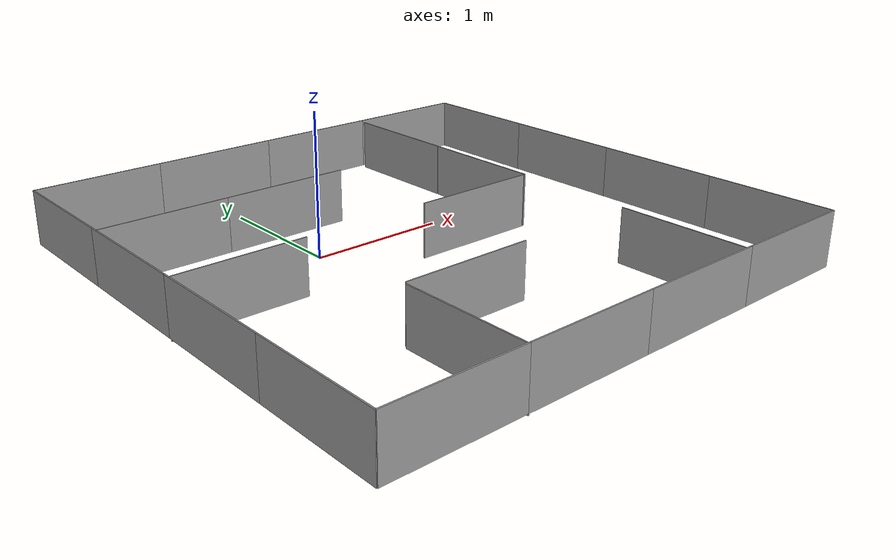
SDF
<sdf version="1.7">
 <model name="turtlebot3_maze">
  <model name="enclosure">
   <model name="wall_section_00">
    <link name="link">
     <inertial>
      <mass>0.2</mass>
      <inertia>
       <ixx>0.0333333</ixx>
       <ixy>0</ixy>
       <ixz>0</ixz>
       <iyy>0.0333333</iyy>
       <iyz>0</iyz>
       <izz>0.0333333</izz>
      </inertia>
      <pose>0 0 0 0 -0 0</pose>
     </inertial>
     <self_collide>0</self_collide>
     <enable_wind>0</enable_wind>
     <kinematic>0</kinematic>
     <pose>0 0 0 0 -0 0</pose>
     <gravity>1</gravity>
     <visual name="visual">
      <geometry>
       <box>
        <size>1 0.01 0.42</size>
       </box>
      </geometry>
      <material>
       <script>
        <name>Gazebo/Grey</name>
        <uri>file://media/materials/scripts/gazebo.material</uri>
       </script>
       <shader type="pixel">
        <normal_map>__default__</normal_map>
       </shader>
       <ambient>0.3 0.3 0.3 1</ambient>
       <diffuse>0.7 0.7 0.7 1</diffuse>
       <specular>0.01 0.01 0.01 1</specular>
       <emissive>1 1 1 1</emissive>
      </material>
      <pose>0 0 0 0 -0 0</pose>
      <transparency>0</transparency>
      <cast_shadows>1</cast_shadows>
     </visual>
     <collision name="collision_1">
      <laser_retro>0</laser_retro>
      <max_contacts>10</max_contacts>
      <pose>0 0 0 0 -0 0</pose>
      <geometry>
       <box>
        <size>1 0.01 0.42</size>
       </box>
      </geometry>
      <surface>
       <friction>
        <ode>
         <mu>1</mu>
         <mu2>1</mu2>
         <fdir1>0 0 0</fdir1>
         <slip1>0</slip1>
         <slip2>0</slip2>
        </ode>
        <torsional>
         <coefficient>1</coefficient>
         <patch_radius>0</patch_radius>
         <surface_radius>0</surface_radius>
         <use_patch_radius>1</use_patch_radius>
         <ode>
          <slip>0</slip>
         </ode>
        </torsional>
       </friction>
       <bounce>
        <restitution_coefficient>0</restitution_coefficient>
        <threshold>1e+06</threshold>
       </bounce>
       <contact>
        <collide_without_contact>0</collide_without_contact>
        <collide_without_contact_bitmask>1</collide_without_contact_bitmask>
        <collide_bitmask>1</collide_bitmask>
        <ode>
         <soft_cfm>0</soft_cfm>
         <soft_erp>0.2</soft_erp>
         <kp>1e+13</kp>
         <kd>1</kd>
         <max_vel>0.01</max_vel>
         <min_depth>0</min_depth>
        </ode>
        <bullet>
         <split_impulse>1</split_impulse>
         <split_impulse_penetration_threshold>-0.01</split_impulse_penetration_threshold>
         <soft_cfm>0</soft_cfm>
         <soft_erp>0.2</soft_erp>
         <kp>1e+13</kp>
         <kd>1</kd>
        </bullet>
       </contact>
      </surface>
     </collision>
    </link>
    <static>0</static>
    <allow_auto_disable>1</allow_auto_disable>
    <pose>-0.5 0 0 0 -0 0</pose>
   </model>
   <model name="wall_section_01">
    <link name="link">
     <inertial>
      <mass>0.2</mass>
      <inertia>
       <ixx>0.0333333</ixx>
       <ixy>0</ixy>
       <ixz>0</ixz>
       <iyy>0.0333333</iyy>
       <iyz>0</iyz>
       <izz>0.0333333</izz>
      </inertia>
      <pose>0 0 0 0 -0 0</pose>
     </inertial>
     <self_collide>0</self_collide>
     <enable_wind>0</enable_wind>
     <kinematic>0</kinematic>
     <pose>0 0 0 0 -0 0</pose>
     <gravity>1</gravity>
     <visual name="visual">
      <geometry>
       <box>
        <size>1 0.01 0.42</size>
       </box>
      </geometry>
      <material>
       <script>
        <name>Gazebo/Grey</name>
        <uri>file://media/materials/scripts/gazebo.material</uri>
       </script>
       <shader type="pixel">
        <normal_map>__default__</normal_map>
       </shader>
       <ambient>0.3 0.3 0.3 1</ambient>
       <diffuse>0.7 0.7 0.7 1</diffuse>
       <specular>0.01 0.01 0.01 1</specular>
       <emissive>1 1 1 1</emissive>
      </material>
      <pose>0 0 0 0 -0 0</pose>
      <transparency>0</transparency>
      <cast_shadows>1</cast_shadows>
     </visual>
     <collision name="collision_1">
      <laser_retro>0</laser_retro>
      <max_contacts>10</max_contacts>
      <pose>0 0 0 0 -0 0</pose>
      <geometry>
       <box>
        <size>1 0.01 0.42</size>
       </box>
      </geometry>
      <surface>
       <friction>
        <ode>
         <mu>1</mu>
         <mu2>1</mu2>
         <fdir1>0 0 0</fdir1>
         <slip1>0</slip1>
         <slip2>0</slip2>
        </ode>
        <torsional>
         <coefficient>1</coefficient>
         <patch_radius>0</patch_radius>
         <surface_radius>0</surface_radius>
         <use_patch_radius>1</use_patch_radius>
         <ode>
          <slip>0</slip>
         </ode>
        </torsional>
       </friction>
       <bounce>
        <restitution_coefficient>0</restitution_coefficient>
        <threshold>1e+06</threshold>
       </bounce>
       <contact>
        <collide_without_contact>0</collide_without_contact>
        <collide_without_contact_bitmask>1</collide_without_contact_bitmask>
        <collide_bitmask>1</collide_bitmask>
        <ode>
         <soft_cfm>0</soft_cfm>
         <soft_erp>0.2</soft_erp>
         <kp>1e+13</kp>
         <kd>1</kd>
         <max_vel>0.01</max_vel>
         <min_depth>0</min_depth>
        </ode>
        <bullet>
         <split_impulse>1</split_impulse>
         <split_impulse_penetration_threshold>-0.01</split_impulse_penetration_threshold>
         <soft_cfm>0</soft_cfm>
         <soft_erp>0.2</soft_erp>
         <kp>1e+13</kp>
         <kd>1</kd>
        </bullet>
       </contact>
      </surface>
     </collision>
    </link>
    <static>0</static>
    <allow_auto_disable>1</allow_auto_disable>
    <pose>0.5 0 0 0 -0 0</pose>
   </model>
   <model name="wall_section_02">
    <link name="link">
     <inertial>
      <mass>0.2</mass>
      <inertia>
       <ixx>0.0333333</ixx>
       <ixy>0</ixy>
       <ixz>0</ixz>
       <iyy>0.0333333</iyy>
       <iyz>0</iyz>
       <izz>0.0333333</izz>
      </inertia>
      <pose>0 0 0 0 -0 0</pose>
     </inertial>
     <self_collide>0</self_collide>
     <enable_wind>0</enable_wind>
     <kinematic>0</kinematic>
     <pose>0 0 0 0 -0 0</pose>
     <gravity>1</gravity>
     <visual name="visual">
      <geometry>
       <box>
        <size>1 0.01 0.42</size>
       </box>
      </geometry>
      <material>
       <script>
        <name>Gazebo/Grey</name>
        <uri>file://media/materials/scripts/gazebo.material</uri>
       </script>
       <shader type="pixel">
        <normal_map>__default__</normal_map>
       </shader>
       <ambient>0.3 0.3 0.3 1</ambient>
       <diffuse>0.7 0.7 0.7 1</diffuse>
       <specular>0.01 0.01 0.01 1</specular>
       <emissive>1 1 1 1</emissive>
      </material>
      <pose>0 0 0 0 -0 0</pose>
      <transparency>0</transparency>
      <cast_shadows>1</cast_shadows>
     </visual>
     <collision name="collision_1">
      <laser_retro>0</laser_retro>
      <max_contacts>10</max_contacts>
      <pose>0 0 0 0 -0 0</pose>
      <geometry>
       <box>
        <size>1 0.01 0.42</size>
       </box>
      </geometry>
      <surface>
       <friction>
        <ode>
         <mu>1</mu>
         <mu2>1</mu2>
         <fdir1>0 0 0</fdir1>
         <slip1>0</slip1>
         <slip2>0</slip2>
        </ode>
        <torsional>
         <coefficient>1</coefficient>
         <patch_radius>0</patch_radius>
         <surface_radius>0</surface_radius>
         <use_patch_radius>1</use_patch_radius>
         <ode>
          <slip>0</slip>
         </ode>
        </torsional>
       </friction>
       <bounce>
        <restitution_coefficient>0</restitution_coefficient>
        <threshold>1e+06</threshold>
       </bounce>
       <contact>
        <collide_without_contact>0</collide_without_contact>
        <collide_without_contact_bitmask>1</collide_without_contact_bitmask>
        <collide_bitmask>1</collide_bitmask>
        <ode>
         <soft_cfm>0</soft_cfm>
         <soft_erp>0.2</soft_erp>
         <kp>1e+13</kp>
         <kd>1</kd>
         <max_vel>0.01</max_vel>
         <min_depth>0</min_depth>
        </ode>
        <bullet>
         <split_impulse>1</split_impulse>
         <split_impulse_penetration_threshold>-0.01</split_impulse_penetration_threshold>
         <soft_cfm>0</soft_cfm>
         <soft_erp>0.2</soft_erp>
         <kp>1e+13</kp>
         <kd>1</kd>
        </bullet>
       </contact>
      </surface>
     </collision>
    </link>
    <static>0</static>
    <allow_auto_disable>1</allow_auto_disable>
    <pose>1.5 0 0 0 -0 0</pose>
   </model>
   <model name="wall_section_03">
    <link name="link">
     <inertial>
      <mass>0.2</mass>
      <inertia>
       <ixx>0.0333333</ixx>
       <ixy>0</ixy>
       <ixz>0</ixz>
       <iyy>0.0333333</iyy>
       <iyz>0</iyz>
       <izz>0.0333333</izz>
      </inertia>
      <pose>0 0 0 0 -0 0</pose>
     </inertial>
     <self_collide>0</self_collide>
     <enable_wind>0</enable_wind>
     <kinematic>0</kinematic>
     <pose>0 0 0 0 -0 0</pose>
     <gravity>1</gravity>
     <visual name="visual">
      <geometry>
       <box>
        <size>1 0.01 0.42</size>
       </box>
      </geometry>
      <material>
       <script>
        <name>Gazebo/Grey</name>
        <uri>file://media/materials/scripts/gazebo.material</uri>
       </script>
       <shader type="pixel">
        <normal_map>__default__</normal_map>
       </shader>
       <ambient>0.3 0.3 0.3 1</ambient>
       <diffuse>0.7 0.7 0.7 1</diffuse>
       <specular>0.01 0.01 0.01 1</specular>
       <emissive>1 1 1 1</emissive>
      </material>
      <pose>0 0 0 0 -0 0</pose>
      <transparency>0</transparency>
      <cast_shadows>1</cast_shadows>
     </visual>
     <collision name="collision_1">
      <laser_retro>0</laser_retro>
      <max_contacts>10</max_contacts>
      <pose>0 0 0 0 -0 0</pose>
      <geometry>
       <box>
        <size>1 0.01 0.42</size>
       </box>
      </geometry>
      <surface>
       <friction>
        <ode>
         <mu>1</mu>
         <mu2>1</mu2>
         <fdir1>0 0 0</fdir1>
         <slip1>0</slip1>
         <slip2>0</slip2>
        </ode>
        <torsional>
         <coefficient>1</coefficient>
         <patch_radius>0</patch_radius>
         <surface_radius>0</surface_radius>
         <use_patch_radius>1</use_patch_radius>
         <ode>
          <slip>0</slip>
         </ode>
        </torsional>
       </friction>
       <bounce>
        <restitution_coefficient>0</restitution_coefficient>
        <threshold>1e+06</threshold>
       </bounce>
       <contact>
        <collide_without_contact>0</collide_without_contact>
        <collide_without_contact_bitmask>1</collide_without_contact_bitmask>
        <collide_bitmask>1</collide_bitmask>
        <ode>
         <soft_cfm>0</soft_cfm>
         <soft_erp>0.2</soft_erp>
         <kp>1e+13</kp>
         <kd>1</kd>
         <max_vel>0.01</max_vel>
         <min_depth>0</min_depth>
        </ode>
        <bullet>
         <split_impulse>1</split_impulse>
         <split_impulse_penetration_threshold>-0.01</split_impulse_penetration_threshold>
         <soft_cfm>0</soft_cfm>
         <soft_erp>0.2</soft_erp>
         <kp>1e+13</kp>
         <kd>1</kd>
        </bullet>
       </contact>
      </surface>
     </collision>
    </link>
    <static>0</static>
    <allow_auto_disable>1</allow_auto_disable>
    <pose>2.5 0 0 0 -0 0</pose>
   </model>
   <model name="wall_section_04">
    <link name="link">
     <inertial>
      <mass>0.2</mass>
      <inertia>
       <ixx>0.0333333</ixx>
       <ixy>0</ixy>
       <ixz>0</ixz>
       <iyy>0.0333333</iyy>
       <iyz>0</iyz>
       <izz>0.0333333</izz>
      </inertia>
      <pose>0 0 0 0 -0 0</pose>
     </inertial>
     <self_collide>0</self_collide>
     <enable_wind>0</enable_wind>
     <kinematic>0</kinematic>
     <pose>0 0 0 0 -0 0</pose>
     <gravity>1</gravity>
     <visual name="visual">
      <geometry>
       <box>
        <size>1 0.01 0.42</size>
       </box>
      </geometry>
      <material>
       <script>
        <name>Gazebo/Grey</name>
        <uri>file://media/materials/scripts/gazebo.material</uri>
       </script>
       <shader type="pixel">
        <normal_map>__default__</normal_map>
       </shader>
       <ambient>0.3 0.3 0.3 1</ambient>
       <diffuse>0.7 0.7 0.7 1</diffuse>
       <specular>0.01 0.01 0.01 1</specular>
       <emissive>1 1 1 1</emissive>
      </material>
      <pose>0 0 0 0 -0 0</pose>
      <transparency>0</transparency>
      <cast_shadows>1</cast_shadows>
     </visual>
     <collision name="collision_1">
      <laser_retro>0</laser_retro>
      <max_contacts>10</max_contacts>
      <pose>0 0 0 0 -0 0</pose>
      <geometry>
       <box>
        <size>1 0.01 0.42</size>
       </box>
      </geometry>
      <surface>
       <friction>
        <ode>
         <mu>1</mu>
         <mu2>1</mu2>
         <fdir1>0 0 0</fdir1>
         <slip1>0</slip1>
         <slip2>0</slip2>
        </ode>
        <torsional>
         <coefficient>1</coefficient>
         <patch_radius>0</patch_radius>
         <surface_radius>0</surface_radius>
         <use_patch_radius>1</use_patch_radius>
         <ode>
          <slip>0</slip>
         </ode>
        </torsional>
       </friction>
       <bounce>
        <restitution_coefficient>0</restitution_coefficient>
        <threshold>1e+06</threshold>
       </bounce>
       <contact>
        <collide_without_contact>0</collide_without_contact>
        <collide_without_contact_bitmask>1</collide_without_contact_bitmask>
        <collide_bitmask>1</collide_bitmask>
        <ode>
         <soft_cfm>0</soft_cfm>
         <soft_erp>0.2</soft_erp>
         <kp>1e+13</kp>
         <kd>1</kd>
         <max_vel>0.01</max_vel>
         <min_depth>0</min_depth>
        </ode>
        <bullet>
         <split_impulse>1</split_impulse>
         <split_impulse_penetration_threshold>-0.01</split_impulse_penetration_threshold>
         <soft_cfm>0</soft_cfm>
         <soft_erp>0.2</soft_erp>
         <kp>1e+13</kp>
         <kd>1</kd>
        </bullet>
       </contact>
      </surface>
     </collision>
    </link>
    <static>0</static>
    <allow_auto_disable>1</allow_auto_disable>
    <pose>3 0.5 0 0 -0 1.5708</pose>
   </model>
   <model name="wall_section_05">
    <link name="link">
     <inertial>
      <mass>0.2</mass>
      <inertia>
       <ixx>0.0333333</ixx>
       <ixy>0</ixy>
       <ixz>0</ixz>
       <iyy>0.0333333</iyy>
       <iyz>0</iyz>
       <izz>0.0333333</izz>
      </inertia>
      <pose>0 0 0 0 -0 0</pose>
     </inertial>
     <self_collide>0</self_collide>
     <enable_wind>0</enable_wind>
     <kinematic>0</kinematic>
     <pose>0 0 0 0 -0 0</pose>
     <gravity>1</gravity>
     <visual name="visual">
      <geometry>
       <box>
        <size>1 0.01 0.42</size>
       </box>
      </geometry>
      <material>
       <script>
        <name>Gazebo/Grey</name>
        <uri>file://media/materials/scripts/gazebo.material</uri>
       </script>
       <shader type="pixel">
        <normal_map>__default__</normal_map>
       </shader>
       <ambient>0.3 0.3 0.3 1</ambient>
       <diffuse>0.7 0.7 0.7 1</diffuse>
       <specular>0.01 0.01 0.01 1</specular>
       <emissive>1 1 1 1</emissive>
      </material>
      <pose>0 0 0 0 -0 0</pose>
      <transparency>0</transparency>
      <cast_shadows>1</cast_shadows>
     </visual>
     <collision name="collision_1">
      <laser_retro>0</laser_retro>
      <max_contacts>10</max_contacts>
      <pose>0 0 0 0 -0 0</pose>
      <geometry>
       <box>
        <size>1 0.01 0.42</size>
       </box>
      </geometry>
      <surface>
       <friction>
        <ode>
         <mu>1</mu>
         <mu2>1</mu2>
         <fdir1>0 0 0</fdir1>
         <slip1>0</slip1>
         <slip2>0</slip2>
        </ode>
        <torsional>
         <coefficient>1</coefficient>
         <patch_radius>0</patch_radius>
         <surface_radius>0</surface_radius>
         <use_patch_radius>1</use_patch_radius>
         <ode>
          <slip>0</slip>
         </ode>
        </torsional>
       </friction>
       <bounce>
        <restitution_coefficient>0</restitution_coefficient>
        <threshold>1e+06</threshold>
       </bounce>
       <contact>
        <collide_without_contact>0</collide_without_contact>
        <collide_without_contact_bitmask>1</collide_without_contact_bitmask>
        <collide_bitmask>1</collide_bitmask>
        <ode>
         <soft_cfm>0</soft_cfm>
         <soft_erp>0.2</soft_erp>
         <kp>1e+13</kp>
         <kd>1</kd>
         <max_vel>0.01</max_vel>
         <min_depth>0</min_depth>
        </ode>
        <bullet>
         <split_impulse>1</split_impulse>
         <split_impulse_penetration_threshold>-0.01</split_impulse_penetration_threshold>
         <soft_cfm>0</soft_cfm>
         <soft_erp>0.2</soft_erp>
         <kp>1e+13</kp>
         <kd>1</kd>
        </bullet>
       </contact>
      </surface>
     </collision>
    </link>
    <static>0</static>
    <allow_auto_disable>1</allow_auto_disable>
    <pose>3 1.5 0 0 -0 1.5708</pose>
   </model>
   <model name="wall_section_06">
    <link name="link">
     <inertial>
      <mass>0.2</mass>
      <inertia>
       <ixx>0.0333333</ixx>
       <ixy>0</ixy>
       <ixz>0</ixz>
       <iyy>0.0333333</iyy>
       <iyz>0</iyz>
       <izz>0.0333333</izz>
      </inertia>
      <pose>0 0 0 0 -0 0</pose>
     </inertial>
     <self_collide>0</self_collide>
     <enable_wind>0</enable_wind>
     <kinematic>0</kinematic>
     <pose>0 0 0 0 -0 0</pose>
     <gravity>1</gravity>
     <visual name="visual">
      <geometry>
       <box>
        <size>1 0.01 0.42</size>
       </box>
      </geometry>
      <material>
       <script>
        <name>Gazebo/Grey</name>
        <uri>file://media/materials/scripts/gazebo.material</uri>
       </script>
       <shader type="pixel">
        <normal_map>__default__</normal_map>
       </shader>
       <ambient>0.3 0.3 0.3 1</ambient>
       <diffuse>0.7 0.7 0.7 1</diffuse>
       <specular>0.01 0.01 0.01 1</specular>
       <emissive>1 1 1 1</emissive>
      </material>
      <pose>0 0 0 0 -0 0</pose>
      <transparency>0</transparency>
      <cast_shadows>1</cast_shadows>
     </visual>
     <collision name="collision_1">
      <laser_retro>0</laser_retro>
      <max_contacts>10</max_contacts>
      <pose>0 0 0 0 -0 0</pose>
      <geometry>
       <box>
        <size>1 0.01 0.42</size>
       </box>
      </geometry>
      <surface>
       <friction>
        <ode>
         <mu>1</mu>
         <mu2>1</mu2>
         <fdir1>0 0 0</fdir1>
         <slip1>0</slip1>
         <slip2>0</slip2>
        </ode>
        <torsional>
         <coefficient>1</coefficient>
         <patch_radius>0</patch_radius>
         <surface_radius>0</surface_radius>
         <use_patch_radius>1</use_patch_radius>
         <ode>
          <slip>0</slip>
         </ode>
        </torsional>
       </friction>
       <bounce>
        <restitution_coefficient>0</restitution_coefficient>
        <threshold>1e+06</threshold>
       </bounce>
       <contact>
        <collide_without_contact>0</collide_without_contact>
        <collide_without_contact_bitmask>1</collide_without_contact_bitmask>
        <collide_bitmask>1</collide_bitmask>
        <ode>
         <soft_cfm>0</soft_cfm>
         <soft_erp>0.2</soft_erp>
         <kp>1e+13</kp>
         <kd>1</kd>
         <max_vel>0.01</max_vel>
         <min_depth>0</min_depth>
        </ode>
        <bullet>
         <split_impulse>1</split_impulse>
         <split_impulse_penetration_threshold>-0.01</split_impulse_penetration_threshold>
         <soft_cfm>0</soft_cfm>
         <soft_erp>0.2</soft_erp>
         <kp>1e+13</kp>
         <kd>1</kd>
        </bullet>
       </contact>
      </surface>
     </collision>
    </link>
    <static>0</static>
    <allow_auto_disable>1</allow_auto_disable>
    <pose>3 2.5 0 0 -0 1.5708</pose>
   </model>
   <model name="wall_section_07">
    <link name="link">
     <inertial>
      <mass>0.2</mass>
      <inertia>
       <ixx>0.0333333</ixx>
       <ixy>0</ixy>
       <ixz>0</ixz>
       <iyy>0.0333333</iyy>
       <iyz>0</iyz>
       <izz>0.0333333</izz>
      </inertia>
      <pose>0 0 0 0 -0 0</pose>
     </inertial>
     <self_collide>0</self_collide>
     <enable_wind>0</enable_wind>
     <kinematic>0</kinematic>
     <pose>0 0 0 0 -0 0</pose>
     <gravity>1</gravity>
     <visual name="visual">
      <geometry>
       <box>
        <size>1 0.01 0.42</size>
       </box>
      </geometry>
      <material>
       <script>
        <name>Gazebo/Grey</name>
        <uri>file://media/materials/scripts/gazebo.material</uri>
       </script>
       <shader type="pixel">
        <normal_map>__default__</normal_map>
       </shader>
       <ambient>0.3 0.3 0.3 1</ambient>
       <diffuse>0.7 0.7 0.7 1</diffuse>
       <specular>0.01 0.01 0.01 1</specular>
       <emissive>1 1 1 1</emissive>
      </material>
      <pose>0 0 0 0 -0 0</pose>
      <transparency>0</transparency>
      <cast_shadows>1</cast_shadows>
     </visual>
     <collision name="collision_1">
      <laser_retro>0</laser_retro>
      <max_contacts>10</max_contacts>
      <pose>0 0 0 0 -0 0</pose>
      <geometry>
       <box>
        <size>1 0.01 0.42</size>
       </box>
      </geometry>
      <surface>
       <friction>
        <ode>
         <mu>1</mu>
         <mu2>1</mu2>
         <fdir1>0 0 0</fdir1>
         <slip1>0</slip1>
         <slip2>0</slip2>
        </ode>
        <torsional>
         <coefficient>1</coefficient>
         <patch_radius>0</patch_radius>
         <surface_radius>0</surface_radius>
         <use_patch_radius>1</use_patch_radius>
         <ode>
          <slip>0</slip>
         </ode>
        </torsional>
       </friction>
       <bounce>
        <restitution_coefficient>0</restitution_coefficient>
        <threshold>1e+06</threshold>
       </bounce>
       <contact>
        <collide_without_contact>0</collide_without_contact>
        <collide_without_contact_bitmask>1</collide_without_contact_bitmask>
        <collide_bitmask>1</collide_bitmask>
        <ode>
         <soft_cfm>0</soft_cfm>
         <soft_erp>0.2</soft_erp>
         <kp>1e+13</kp>
         <kd>1</kd>
         <max_vel>0.01</max_vel>
         <min_depth>0</min_depth>
        </ode>
        <bullet>
         <split_impulse>1</split_impulse>
         <split_impulse_penetration_threshold>-0.01</split_impulse_penetration_threshold>
         <soft_cfm>0</soft_cfm>
         <soft_erp>0.2</soft_erp>
         <kp>1e+13</kp>
         <kd>1</kd>
        </bullet>
       </contact>
      </surface>
     </collision>
    </link>
    <static>0</static>
    <allow_auto_disable>1</allow_auto_disable>
    <pose>3 3.5 0 0 -0 1.5708</pose>
   </model>
   <model name="wall_section_08">
    <link name="link">
     <inertial>
      <mass>0.2</mass>
      <inertia>
       <ixx>0.0333333</ixx>
       <ixy>0</ixy>
       <ixz>0</ixz>
       <iyy>0.0333333</iyy>
       <iyz>0</iyz>
       <izz>0.0333333</izz>
      </inertia>
      <pose>0 0 0 0 -0 0</pose>
     </inertial>
     <self_collide>0</self_collide>
     <enable_wind>0</enable_wind>
     <kinematic>0</kinematic>
     <pose>0 0 0 0 -0 0</pose>
     <gravity>1</gravity>
     <visual name="visual">
      <geometry>
       <box>
        <size>1 0.01 0.42</size>
       </box>
      </geometry>
      <material>
       <script>
        <name>Gazebo/Grey</name>
        <uri>file://media/materials/scripts/gazebo.material</uri>
       </script>
       <shader type="pixel">
        <normal_map>__default__</normal_map>
       </shader>
       <ambient>0.3 0.3 0.3 1</ambient>
       <diffuse>0.7 0.7 0.7 1</diffuse>
       <specular>0.01 0.01 0.01 1</specular>
       <emissive>1 1 1 1</emissive>
      </material>
      <pose>0 0 0 0 -0 0</pose>
      <transparency>0</transparency>
      <cast_shadows>1</cast_shadows>
     </visual>
     <collision name="collision_1">
      <laser_retro>0</laser_retro>
      <max_contacts>10</max_contacts>
      <pose>0 0 0 0 -0 0</pose>
      <geometry>
       <box>
        <size>1 0.01 0.42</size>
       </box>
      </geometry>
      <surface>
       <friction>
        <ode>
         <mu>1</mu>
         <mu2>1</mu2>
         <fdir1>0 0 0</fdir1>
         <slip1>0</slip1>
         <slip2>0</slip2>
        </ode>
        <torsional>
         <coefficient>1</coefficient>
         <patch_radius>0</patch_radius>
         <surface_radius>0</surface_radius>
         <use_patch_radius>1</use_patch_radius>
         <ode>
          <slip>0</slip>
         </ode>
        </torsional>
       </friction>
       <bounce>
        <restitution_coefficient>0</restitution_coefficient>
        <threshold>1e+06</threshold>
       </bounce>
       <contact>
        <collide_without_contact>0</collide_without_contact>
        <collide_without_contact_bitmask>1</collide_without_contact_bitmask>
        <collide_bitmask>1</collide_bitmask>
        <ode>
         <soft_cfm>0</soft_cfm>
         <soft_erp>0.2</soft_erp>
         <kp>1e+13</kp>
         <kd>1</kd>
         <max_vel>0.01</max_vel>
         <min_depth>0</min_depth>
        </ode>
        <bullet>
         <split_impulse>1</split_impulse>
         <split_impulse_penetration_threshold>-0.01</split_impulse_penetration_threshold>
         <soft_cfm>0</soft_cfm>
         <soft_erp>0.2</soft_erp>
         <kp>1e+13</kp>
         <kd>1</kd>
        </bullet>
       </contact>
      </surface>
     </collision>
    </link>
    <static>0</static>
    <allow_auto_disable>1</allow_auto_disable>
    <pose>2.5 4 0 0 -0 3.14159</pose>
   </model>
   <model name="wall_section_09">
    <link name="link">
     <inertial>
      <mass>0.2</mass>
      <inertia>
       <ixx>0.0333333</ixx>
       <ixy>0</ixy>
       <ixz>0</ixz>
       <iyy>0.0333333</iyy>
       <iyz>0</iyz>
       <izz>0.0333333</izz>
      </inertia>
      <pose>0 0 0 0 -0 0</pose>
     </inertial>
     <self_collide>0</self_collide>
     <enable_wind>0</enable_wind>
     <kinematic>0</kinematic>
     <pose>0 0 0 0 -0 0</pose>
     <gravity>1</gravity>
     <visual name="visual">
      <geometry>
       <box>
        <size>1 0.01 0.42</size>
       </box>
      </geometry>
      <material>
       <script>
        <name>Gazebo/Grey</name>
        <uri>file://media/materials/scripts/gazebo.material</uri>
       </script>
       <shader type="pixel">
        <normal_map>__default__</normal_map>
       </shader>
       <ambient>0.3 0.3 0.3 1</ambient>
       <diffuse>0.7 0.7 0.7 1</diffuse>
       <specular>0.01 0.01 0.01 1</specular>
       <emissive>1 1 1 1</emissive>
      </material>
      <pose>0 0 0 0 -0 0</pose>
      <transparency>0</transparency>
      <cast_shadows>1</cast_shadows>
     </visual>
     <collision name="collision_1">
      <laser_retro>0</laser_retro>
      <max_contacts>10</max_contacts>
      <pose>0 0 0 0 -0 0</pose>
      <geometry>
       <box>
        <size>1 0.01 0.42</size>
       </box>
      </geometry>
      <surface>
       <friction>
        <ode>
         <mu>1</mu>
         <mu2>1</mu2>
         <fdir1>0 0 0</fdir1>
         <slip1>0</slip1>
         <slip2>0</slip2>
        </ode>
        <torsional>
         <coefficient>1</coefficient>
         <patch_radius>0</patch_radius>
         <surface_radius>0</surface_radius>
         <use_patch_radius>1</use_patch_radius>
         <ode>
          <slip>0</slip>
         </ode>
        </torsional>
       </friction>
       <bounce>
        <restitution_coefficient>0</restitution_coefficient>
        <threshold>1e+06</threshold>
       </bounce>
       <contact>
        <collide_without_contact>0</collide_without_contact>
        <collide_without_contact_bitmask>1</collide_without_contact_bitmask>
        <collide_bitmask>1</collide_bitmask>
        <ode>
         <soft_cfm>0</soft_cfm>
         <soft_erp>0.2</soft_erp>
         <kp>1e+13</kp>
         <kd>1</kd>
         <max_vel>0.01</max_vel>
         <min_depth>0</min_depth>
        </ode>
        <bullet>
         <split_impulse>1</split_impulse>
         <split_impulse_penetration_threshold>-0.01</split_impulse_penetration_threshold>
         <soft_cfm>0</soft_cfm>
         <soft_erp>0.2</soft_erp>
         <kp>1e+13</kp>
         <kd>1</kd>
        </bullet>
       </contact>
      </surface>
     </collision>
    </link>
    <static>0</static>
    <allow_auto_disable>1</allow_auto_disable>
    <pose>1.5 4 0 0 -0 3.14159</pose>
   </model>
   <model name="wall_section_10">
    <link name="link">
     <inertial>
      <mass>0.2</mass>
      <inertia>
       <ixx>0.0333333</ixx>
       <ixy>0</ixy>
       <ixz>0</ixz>
       <iyy>0.0333333</iyy>
       <iyz>0</iyz>
       <izz>0.0333333</izz>
      </inertia>
      <pose>0 0 0 0 -0 0</pose>
     </inertial>
     <self_collide>0</self_collide>
     <enable_wind>0</enable_wind>
     <kinematic>0</kinematic>
     <pose>0 0 0 0 -0 0</pose>
     <gravity>1</gravity>
     <visual name="visual">
      <geometry>
       <box>
        <size>1 0.01 0.42</size>
       </box>
      </geometry>
      <material>
       <script>
        <name>Gazebo/Grey</name>
        <uri>file://media/materials/scripts/gazebo.material</uri>
       </script>
       <shader type="pixel">
        <normal_map>__default__</normal_map>
       </shader>
       <ambient>0.3 0.3 0.3 1</ambient>
       <diffuse>0.7 0.7 0.7 1</diffuse>
       <specular>0.01 0.01 0.01 1</specular>
       <emissive>1 1 1 1</emissive>
      </material>
      <pose>0 0 0 0 -0 0</pose>
      <transparency>0</transparency>
      <cast_shadows>1</cast_shadows>
     </visual>
     <collision name="collision_1">
      <laser_retro>0</laser_retro>
      <max_contacts>10</max_contacts>
      <pose>0 0 0 0 -0 0</pose>
      <geometry>
       <box>
        <size>1 0.01 0.42</size>
       </box>
      </geometry>
      <surface>
       <friction>
        <ode>
         <mu>1</mu>
         <mu2>1</mu2>
         <fdir1>0 0 0</fdir1>
         <slip1>0</slip1>
         <slip2>0</slip2>
        </ode>
        <torsional>
         <coefficient>1</coefficient>
         <patch_radius>0</patch_radius>
         <surface_radius>0</surface_radius>
         <use_patch_radius>1</use_patch_radius>
         <ode>
          <slip>0</slip>
         </ode>
        </torsional>
       </friction>
       <bounce>
        <restitution_coefficient>0</restitution_coefficient>
        <threshold>1e+06</threshold>
       </bounce>
       <contact>
        <collide_without_contact>0</collide_without_contact>
        <collide_without_contact_bitmask>1</collide_without_contact_bitmask>
        <collide_bitmask>1</collide_bitmask>
        <ode>
         <soft_cfm>0</soft_cfm>
         <soft_erp>0.2</soft_erp>
         <kp>1e+13</kp>
         <kd>1</kd>
         <max_vel>0.01</max_vel>
         <min_depth>0</min_depth>
        </ode>
        <bullet>
         <split_impulse>1</split_impulse>
         <split_impulse_penetration_threshold>-0.01</split_impulse_penetration_threshold>
         <soft_cfm>0</soft_cfm>
         <soft_erp>0.2</soft_erp>
         <kp>1e+13</kp>
         <kd>1</kd>
        </bullet>
       </contact>
      </surface>
     </collision>
    </link>
    <static>0</static>
    <allow_auto_disable>1</allow_auto_disable>
    <pose>0.5 4 0 0 -0 3.14159</pose>
   </model>
   <model name="wall_section_11">
    <link name="link">
     <inertial>
      <mass>0.2</mass>
      <inertia>
       <ixx>0.0333333</ixx>
       <ixy>0</ixy>
       <ixz>0</ixz>
       <iyy>0.0333333</iyy>
       <iyz>0</iyz>
       <izz>0.0333333</izz>
      </inertia>
      <pose>0 0 0 0 -0 0</pose>
     </inertial>
     <self_collide>0</self_collide>
     <enable_wind>0</enable_wind>
     <kinematic>0</kinematic>
     <pose>0 0 0 0 -0 0</pose>
     <gravity>1</gravity>
     <visual name="visual">
      <geometry>
       <box>
        <size>1 0.01 0.42</size>
       </box>
      </geometry>
      <material>
       <script>
        <name>Gazebo/Grey</name>
        <uri>file://media/materials/scripts/gazebo.material</uri>
       </script>
       <shader type="pixel">
        <normal_map>__default__</normal_map>
       </shader>
       <ambient>0.3 0.3 0.3 1</ambient>
       <diffuse>0.7 0.7 0.7 1</diffuse>
       <specular>0.01 0.01 0.01 1</specular>
       <emissive>1 1 1 1</emissive>
      </material>
      <pose>0 0 0 0 -0 0</pose>
      <transparency>0</transparency>
      <cast_shadows>1</cast_shadows>
     </visual>
     <collision name="collision_1">
      <laser_retro>0</laser_retro>
      <max_contacts>10</max_contacts>
      <pose>0 0 0 0 -0 0</pose>
      <geometry>
       <box>
        <size>1 0.01 0.42</size>
       </box>
      </geometry>
      <surface>
       <friction>
        <ode>
         <mu>1</mu>
         <mu2>1</mu2>
         <fdir1>0 0 0</fdir1>
         <slip1>0</slip1>
         <slip2>0</slip2>
        </ode>
        <torsional>
         <coefficient>1</coefficient>
         <patch_radius>0</patch_radius>
         <surface_radius>0</surface_radius>
         <use_patch_radius>1</use_patch_radius>
         <ode>
          <slip>0</slip>
         </ode>
        </torsional>
       </friction>
       <bounce>
        <restitution_coefficient>0</restitution_coefficient>
        <threshold>1e+06</threshold>
       </bounce>
       <contact>
        <collide_without_contact>0</collide_without_contact>
        <collide_without_contact_bitmask>1</collide_without_contact_bitmask>
        <collide_bitmask>1</collide_bitmask>
        <ode>
         <soft_cfm>0</soft_cfm>
         <soft_erp>0.2</soft_erp>
         <kp>1e+13</kp>
         <kd>1</kd>
         <max_vel>0.01</max_vel>
         <min_depth>0</min_depth>
        </ode>
        <bullet>
         <split_impulse>1</split_impulse>
         <split_impulse_penetration_threshold>-0.01</split_impulse_penetration_threshold>
         <soft_cfm>0</soft_cfm>
         <soft_erp>0.2</soft_erp>
         <kp>1e+13</kp>
         <kd>1</kd>
        </bullet>
       </contact>
      </surface>
     </collision>
    </link>
    <static>0</static>
    <allow_auto_disable>1</allow_auto_disable>
    <pose>-0.5 4 0 0 -0 3.14159</pose>
   </model>
   <model name="wall_section_12">
    <link name="link">
     <inertial>
      <mass>0.2</mass>
      <inertia>
       <ixx>0.0333333</ixx>
       <ixy>0</ixy>
       <ixz>0</ixz>
       <iyy>0.0333333</iyy>
       <iyz>0</iyz>
       <izz>0.0333333</izz>
      </inertia>
      <pose>0 0 0 0 -0 0</pose>
     </inertial>
     <self_collide>0</self_collide>
     <enable_wind>0</enable_wind>
     <kinematic>0</kinematic>
     <pose>0 0 0 0 -0 0</pose>
     <gravity>1</gravity>
     <visual name="visual">
      <geometry>
       <box>
        <size>1 0.01 0.42</size>
       </box>
      </geometry>
      <material>
       <script>
        <name>Gazebo/Grey</name>
        <uri>file://media/materials/scripts/gazebo.material</uri>
       </script>
       <shader type="pixel">
        <normal_map>__default__</normal_map>
       </shader>
       <ambient>0.3 0.3 0.3 1</ambient>
       <diffuse>0.7 0.7 0.7 1</diffuse>
       <specular>0.01 0.01 0.01 1</specular>
       <emissive>1 1 1 1</emissive>
      </material>
      <pose>0 0 0 0 -0 0</pose>
      <transparency>0</transparency>
      <cast_shadows>1</cast_shadows>
     </visual>
     <collision name="collision_1">
      <laser_retro>0</laser_retro>
      <max_contacts>10</max_contacts>
      <pose>0 0 0 0 -0 0</pose>
      <geometry>
       <box>
        <size>1 0.01 0.42</size>
       </box>
      </geometry>
      <surface>
       <friction>
        <ode>
         <mu>1</mu>
         <mu2>1</mu2>
         <fdir1>0 0 0</fdir1>
         <slip1>0</slip1>
         <slip2>0</slip2>
        </ode>
        <torsional>
         <coefficient>1</coefficient>
         <patch_radius>0</patch_radius>
         <surface_radius>0</surface_radius>
         <use_patch_radius>1</use_patch_radius>
         <ode>
          <slip>0</slip>
         </ode>
        </torsional>
       </friction>
       <bounce>
        <restitution_coefficient>0</restitution_coefficient>
        <threshold>1e+06</threshold>
       </bounce>
       <contact>
        <collide_without_contact>0</collide_without_contact>
        <collide_without_contact_bitmask>1</collide_without_contact_bitmask>
        <collide_bitmask>1</collide_bitmask>
        <ode>
         <soft_cfm>0</soft_cfm>
         <soft_erp>0.2</soft_erp>
         <kp>1e+13</kp>
         <kd>1</kd>
         <max_vel>0.01</max_vel>
         <min_depth>0</min_depth>
        </ode>
        <bullet>
         <split_impulse>1</split_impulse>
         <split_impulse_penetration_threshold>-0.01</split_impulse_penetration_threshold>
         <soft_cfm>0</soft_cfm>
         <soft_erp>0.2</soft_erp>
         <kp>1e+13</kp>
         <kd>1</kd>
        </bullet>
       </contact>
      </surface>
     </collision>
    </link>
    <static>0</static>
    <allow_auto_disable>1</allow_auto_disable>
    <pose>-1 3.5 0 0 0 -1.5708</pose>
   </model>
   <model name="wall_section_13">
    <link name="link">
     <inertial>
      <mass>0.2</mass>
      <inertia>
       <ixx>0.0333333</ixx>
       <ixy>0</ixy>
       <ixz>0</ixz>
       <iyy>0.0333333</iyy>
       <iyz>0</iyz>
       <izz>0.0333333</izz>
      </inertia>
      <pose>0 0 0 0 -0 0</pose>
     </inertial>
     <self_collide>0</self_collide>
     <enable_wind>0</enable_wind>
     <kinematic>0</kinematic>
     <pose>0 0 0 0 -0 0</pose>
     <gravity>1</gravity>
     <visual name="visual">
      <geometry>
       <box>
        <size>1 0.01 0.42</size>
       </box>
      </geometry>
      <material>
       <script>
        <name>Gazebo/Grey</name>
        <uri>file://media/materials/scripts/gazebo.material</uri>
       </script>
       <shader type="pixel">
        <normal_map>__default__</normal_map>
       </shader>
       <ambient>0.3 0.3 0.3 1</ambient>
       <diffuse>0.7 0.7 0.7 1</diffuse>
       <specular>0.01 0.01 0.01 1</specular>
       <emissive>1 1 1 1</emissive>
      </material>
      <pose>0 0 0 0 -0 0</pose>
      <transparency>0</transparency>
      <cast_shadows>1</cast_shadows>
     </visual>
     <collision name="collision_1">
      <laser_retro>0</laser_retro>
      <max_contacts>10</max_contacts>
      <pose>0 0 0 0 -0 0</pose>
      <geometry>
       <box>
        <size>1 0.01 0.42</size>
       </box>
      </geometry>
      <surface>
       <friction>
        <ode>
         <mu>1</mu>
         <mu2>1</mu2>
         <fdir1>0 0 0</fdir1>
         <slip1>0</slip1>
         <slip2>0</slip2>
        </ode>
        <torsional>
         <coefficient>1</coefficient>
         <patch_radius>0</patch_radius>
         <surface_radius>0</surface_radius>
         <use_patch_radius>1</use_patch_radius>
         <ode>
          <slip>0</slip>
         </ode>
        </torsional>
       </friction>
       <bounce>
        <restitution_coefficient>0</restitution_coefficient>
        <threshold>1e+06</threshold>
       </bounce>
       <contact>
        <collide_without_contact>0</collide_without_contact>
        <collide_without_contact_bitmask>1</collide_without_contact_bitmask>
        <collide_bitmask>1</collide_bitmask>
        <ode>
         <soft_cfm>0</soft_cfm>
         <soft_erp>0.2</soft_erp>
         <kp>1e+13</kp>
         <kd>1</kd>
         <max_vel>0.01</max_vel>
         <min_depth>0</min_depth>
        </ode>
        <bullet>
         <split_impulse>1</split_impulse>
         <split_impulse_penetration_threshold>-0.01</split_impulse_penetration_threshold>
         <soft_cfm>0</soft_cfm>
         <soft_erp>0.2</soft_erp>
         <kp>1e+13</kp>
         <kd>1</kd>
        </bullet>
       </contact>
      </surface>
     </collision>
    </link>
    <static>0</static>
    <allow_auto_disable>1</allow_auto_disable>
    <pose>-1 2.5 0 0 0 -1.5708</pose>
   </model>
   <model name="wall_section_14">
    <link name="link">
     <inertial>
      <mass>0.2</mass>
      <inertia>
       <ixx>0.0333333</ixx>
       <ixy>0</ixy>
       <ixz>0</ixz>
       <iyy>0.0333333</iyy>
       <iyz>0</iyz>
       <izz>0.0333333</izz>
      </inertia>
      <pose>0 0 0 0 -0 0</pose>
     </inertial>
     <self_collide>0</self_collide>
     <enable_wind>0</enable_wind>
     <kinematic>0</kinematic>
     <pose>0 0 0 0 -0 0</pose>
     <gravity>1</gravity>
     <visual name="visual">
      <geometry>
       <box>
        <size>1 0.01 0.42</size>
       </box>
      </geometry>
      <material>
       <script>
        <name>Gazebo/Grey</name>
        <uri>file://media/materials/scripts/gazebo.material</uri>
       </script>
       <shader type="pixel">
        <normal_map>__default__</normal_map>
       </shader>
       <ambient>0.3 0.3 0.3 1</ambient>
       <diffuse>0.7 0.7 0.7 1</diffuse>
       <specular>0.01 0.01 0.01 1</specular>
       <emissive>1 1 1 1</emissive>
      </material>
      <pose>0 0 0 0 -0 0</pose>
      <transparency>0</transparency>
      <cast_shadows>1</cast_shadows>
     </visual>
     <collision name="collision_1">
      <laser_retro>0</laser_retro>
      <max_contacts>10</max_contacts>
      <pose>0 0 0 0 -0 0</pose>
      <geometry>
       <box>
        <size>1 0.01 0.42</size>
       </box>
      </geometry>
      <surface>
       <friction>
        <ode>
         <mu>1</mu>
         <mu2>1</mu2>
         <fdir1>0 0 0</fdir1>
         <slip1>0</slip1>
         <slip2>0</slip2>
        </ode>
        <torsional>
         <coefficient>1</coefficient>
         <patch_radius>0</patch_radius>
         <surface_radius>0</surface_radius>
         <use_patch_radius>1</use_patch_radius>
         <ode>
          <slip>0</slip>
         </ode>
        </torsional>
       </friction>
       <bounce>
        <restitution_coefficient>0</restitution_coefficient>
        <threshold>1e+06</threshold>
       </bounce>
       <contact>
        <collide_without_contact>0</collide_without_contact>
        <collide_without_contact_bitmask>1</collide_without_contact_bitmask>
        <collide_bitmask>1</collide_bitmask>
        <ode>
         <soft_cfm>0</soft_cfm>
         <soft_erp>0.2</soft_erp>
         <kp>1e+13</kp>
         <kd>1</kd>
         <max_vel>0.01</max_vel>
         <min_depth>0</min_depth>
        </ode>
        <bullet>
         <split_impulse>1</split_impulse>
         <split_impulse_penetration_threshold>-0.01</split_impulse_penetration_threshold>
         <soft_cfm>0</soft_cfm>
         <soft_erp>0.2</soft_erp>
         <kp>1e+13</kp>
         <kd>1</kd>
        </bullet>
       </contact>
      </surface>
     </collision>
    </link>
    <static>0</static>
    <allow_auto_disable>1</allow_auto_disable>
    <pose>-1 1.5 0 0 0 -1.57079</pose>
   </model>
   <model name="wall_section_15">
    <link name="link">
     <inertial>
      <mass>0.2</mass>
      <inertia>
       <ixx>0.0333333</ixx>
       <ixy>0</ixy>
       <ixz>0</ixz>
       <iyy>0.0333333</iyy>
       <iyz>0</iyz>
       <izz>0.0333333</izz>
      </inertia>
      <pose>0 0 0 0 -0 0</pose>
     </inertial>
     <self_collide>0</self_collide>
     <enable_wind>0</enable_wind>
     <kinematic>0</kinematic>
     <pose>0 0 0 0 -0 0</pose>
     <gravity>1</gravity>
     <visual name="visual">
      <geometry>
       <box>
        <size>1 0.01 0.42</size>
       </box>
      </geometry>
      <material>
       <script>
        <name>Gazebo/Grey</name>
        <uri>file://media/materials/scripts/gazebo.material</uri>
       </script>
       <shader type="pixel">
        <normal_map>__default__</normal_map>
       </shader>
       <ambient>0.3 0.3 0.3 1</ambient>
       <diffuse>0.7 0.7 0.7 1</diffuse>
       <specular>0.01 0.01 0.01 1</specular>
       <emissive>1 1 1 1</emissive>
      </material>
      <pose>0 0 0 0 -0 0</pose>
      <transparency>0</transparency>
      <cast_shadows>1</cast_shadows>
     </visual>
     <collision name="collision_1">
      <laser_retro>0</laser_retro>
      <max_contacts>10</max_contacts>
      <pose>0 0 0 0 -0 0</pose>
      <geometry>
       <box>
        <size>1 0.01 0.42</size>
       </box>
      </geometry>
      <surface>
       <friction>
        <ode>
         <mu>1</mu>
         <mu2>1</mu2>
         <fdir1>0 0 0</fdir1>
         <slip1>0</slip1>
         <slip2>0</slip2>
        </ode>
        <torsional>
         <coefficient>1</coefficient>
         <patch_radius>0</patch_radius>
         <surface_radius>0</surface_radius>
         <use_patch_radius>1</use_patch_radius>
         <ode>
          <slip>0</slip>
         </ode>
        </torsional>
       </friction>
       <bounce>
        <restitution_coefficient>0</restitution_coefficient>
        <threshold>1e+06</threshold>
       </bounce>
       <contact>
        <collide_without_contact>0</collide_without_contact>
        <collide_without_contact_bitmask>1</collide_without_contact_bitmask>
        <collide_bitmask>1</collide_bitmask>
        <ode>
         <soft_cfm>0</soft_cfm>
         <soft_erp>0.2</soft_erp>
         <kp>1e+13</kp>
         <kd>1</kd>
         <max_vel>0.01</max_vel>
         <min_depth>0</min_depth>
        </ode>
        <bullet>
         <split_impulse>1</split_impulse>
         <split_impulse_penetration_threshold>-0.01</split_impulse_penetration_threshold>
         <soft_cfm>0</soft_cfm>
         <soft_erp>0.2</soft_erp>
         <kp>1e+13</kp>
         <kd>1</kd>
        </bullet>
       </contact>
      </surface>
     </collision>
    </link>
    <static>0</static>
    <allow_auto_disable>1</allow_auto_disable>
    <pose>-1 0.5 0 0 0 -1.5708</pose>
   </model>
   <static>0</static>
   <allow_auto_disable>1</allow_auto_disable>
   <pose>-0.153677 -2.06617 0.021892 0 -0 0</pose>
  </model>
  <model name="wall_section">
   <link name="link">
    <inertial>
     <mass>0.2</mass>
     <inertia>
      <ixx>0.0333333</ixx>
      <ixy>0</ixy>
      <ixz>0</ixz>
      <iyy>0.0333333</iyy>
      <iyz>0</iyz>
      <izz>0.0333333</izz>
     </inertia>
     <pose>0 0 0 0 -0 0</pose>
    </inertial>
    <self_collide>0</self_collide>
    <enable_wind>0</enable_wind>
    <kinematic>0</kinematic>
    <pose>0 0 0 0 -0 0</pose>
    <gravity>1</gravity>
    <visual name="visual">
     <geometry>
      <box>
       <size>1 0.01 0.42</size>
      </box>
     </geometry>
     <material>
      <script>
       <name>Gazebo/Grey</name>
       <uri>file://media/materials/scripts/gazebo.material</uri>
      </script>
      <shader type="pixel">
       <normal_map>__default__</normal_map>
      </shader>
      <ambient>0.3 0.3 0.3 1</ambient>
      <diffuse>0.7 0.7 0.7 1</diffuse>
      <specular>0.01 0.01 0.01 1</specular>
      <emissive>1 1 1 1</emissive>
     </material>
     <pose>0 0 0 0 -0 0</pose>
     <transparency>0</transparency>
     <cast_shadows>1</cast_shadows>
    </visual>
    <collision name="collision_1">
     <laser_retro>0</laser_retro>
     <max_contacts>10</max_contacts>
     <pose>0 0 0 0 -0 0</pose>
     <geometry>
      <box>
       <size>1 0.01 0.42</size>
      </box>
     </geometry>
     <surface>
      <friction>
       <ode>
        <mu>1</mu>
        <mu2>1</mu2>
        <fdir1>0 0 0</fdir1>
        <slip1>0</slip1>
        <slip2>0</slip2>
       </ode>
       <torsional>
        <coefficient>1</coefficient>
        <patch_radius>0</patch_radius>
        <surface_radius>0</surface_radius>
        <use_patch_radius>1</use_patch_radius>
        <ode>
         <slip>0</slip>
        </ode>
       </torsional>
      </friction>
      <bounce>
       <restitution_coefficient>0</restitution_coefficient>
       <threshold>1e+06</threshold>
      </bounce>
      <contact>
       <collide_without_contact>0</collide_without_contact>
       <collide_without_contact_bitmask>1</collide_without_contact_bitmask>
       <collide_bitmask>1</collide_bitmask>
       <ode>
        <soft_cfm>0</soft_cfm>
        <soft_erp>0.2</soft_erp>
        <kp>1e+13</kp>
        <kd>1</kd>
        <max_vel>0.01</max_vel>
        <min_depth>0</min_depth>
       </ode>
       <bullet>
        <split_impulse>1</split_impulse>
        <split_impulse_penetration_threshold>-0.01</split_impulse_penetration_threshold>
        <soft_cfm>0</soft_cfm>
        <soft_erp>0.2</soft_erp>
        <kp>1e+13</kp>
        <kd>1</kd>
       </bullet>
      </contact>
     </surface>
    </collision>
   </link>
   <static>0</static>
   <allow_auto_disable>1</allow_auto_disable>
   <pose>-0.638144 0.932565 1e-05 0 -0 0</pose>
  </model>
  <model name="wall_section_0">
   <link name="link">
    <inertial>
     <mass>0.2</mass>
     <inertia>
      <ixx>0.0333333</ixx>
      <ixy>0</ixy>
      <ixz>0</ixz>
      <iyy>0.0333333</iyy>
      <iyz>0</iyz>
      <izz>0.0333333</izz>
     </inertia>
     <pose>0 0 0 0 -0 0</pose>
    </inertial>
    <self_collide>0</self_collide>
    <enable_wind>0</enable_wind>
    <kinematic>0</kinematic>
    <pose>0 0 0 0 -0 0</pose>
    <gravity>1</gravity>
    <visual name="visual">
     <geometry>
      <box>
       <size>1 0.01 0.42</size>
      </box>
     </geometry>
     <material>
      <script>
       <name>Gazebo/Grey</name>
       <uri>file://media/materials/scripts/gazebo.material</uri>
      </script>
      <shader type="pixel">
       <normal_map>__default__</normal_map>
      </shader>
      <ambient>0.3 0.3 0.3 1</ambient>
      <diffuse>0.7 0.7 0.7 1</diffuse>
      <specular>0.01 0.01 0.01 1</specular>
      <emissive>1 1 1 1</emissive>
     </material>
     <pose>0 0 0 0 -0 0</pose>
     <transparency>0</transparency>
     <cast_shadows>1</cast_shadows>
    </visual>
    <collision name="collision_1">
     <laser_retro>0</laser_retro>
     <max_contacts>10</max_contacts>
     <pose>0 0 0 0 -0 0</pose>
     <geometry>
      <box>
       <size>1 0.01 0.42</size>
      </box>
     </geometry>
     <surface>
      <friction>
       <ode>
        <mu>1</mu>
        <mu2>1</mu2>
        <fdir1>0 0 0</fdir1>
        <slip1>0</slip1>
        <slip2>0</slip2>
       </ode>
       <torsional>
        <coefficient>1</coefficient>
        <patch_radius>0</patch_radius>
        <surface_radius>0</surface_radius>
        <use_patch_radius>1</use_patch_radius>
        <ode>
         <slip>0</slip>
        </ode>
       </torsional>
      </friction>
      <bounce>
       <restitution_coefficient>0</restitution_coefficient>
       <threshold>1e+06</threshold>
      </bounce>
      <contact>
       <collide_without_contact>0</collide_without_contact>
       <collide_without_contact_bitmask>1</collide_without_contact_bitmask>
       <collide_bitmask>1</collide_bitmask>
       <ode>
        <soft_cfm>0</soft_cfm>
        <soft_erp>0.2</soft_erp>
        <kp>1e+13</kp>
        <kd>1</kd>
        <max_vel>0.01</max_vel>
        <min_depth>0</min_depth>
       </ode>
       <bullet>
        <split_impulse>1</split_impulse>
        <split_impulse_penetration_threshold>-0.01</split_impulse_penetration_threshold>
        <soft_cfm>0</soft_cfm>
        <soft_erp>0.2</soft_erp>
        <kp>1e+13</kp>
        <kd>1</kd>
       </bullet>
      </contact>
     </surface>
    </collision>
   </link>
   <static>0</static>
   <allow_auto_disable>1</allow_auto_disable>
   <pose>0.361885 0.932594 1.2e-05 0 -0 0</pose>
  </model>
  <model name="wall_section_1">
   <link name="link">
    <inertial>
     <mass>0.2</mass>
     <inertia>
      <ixx>0.0333333</ixx>
      <ixy>0</ixy>
      <ixz>0</ixz>
      <iyy>0.0333333</iyy>
      <iyz>0</iyz>
      <izz>0.0333333</izz>
     </inertia>
     <pose>0 0 0 0 -0 0</pose>
    </inertial>
    <self_collide>0</self_collide>
    <enable_wind>0</enable_wind>
    <kinematic>0</kinematic>
    <pose>0 0 0 0 -0 0</pose>
    <gravity>1</gravity>
    <visual name="visual">
     <geometry>
      <box>
       <size>1 0.01 0.42</size>
      </box>
     </geometry>
     <material>
      <script>
       <name>Gazebo/Grey</name>
       <uri>file://media/materials/scripts/gazebo.material</uri>
      </script>
      <shader type="pixel">
       <normal_map>__default__</normal_map>
      </shader>
      <ambient>0.3 0.3 0.3 1</ambient>
      <diffuse>0.7 0.7 0.7 1</diffuse>
      <specular>0.01 0.01 0.01 1</specular>
      <emissive>1 1 1 1</emissive>
     </material>
     <pose>0 0 0 0 -0 0</pose>
     <transparency>0</transparency>
     <cast_shadows>1</cast_shadows>
    </visual>
    <collision name="collision_1">
     <laser_retro>0</laser_retro>
     <max_contacts>10</max_contacts>
     <pose>0 0 0 0 -0 0</pose>
     <geometry>
      <box>
       <size>1 0.01 0.42</size>
      </box>
     </geometry>
     <surface>
      <friction>
       <ode>
        <mu>1</mu>
        <mu2>1</mu2>
        <fdir1>0 0 0</fdir1>
        <slip1>0</slip1>
        <slip2>0</slip2>
       </ode>
       <torsional>
        <coefficient>1</coefficient>
        <patch_radius>0</patch_radius>
        <surface_radius>0</surface_radius>
        <use_patch_radius>1</use_patch_radius>
        <ode>
         <slip>0</slip>
        </ode>
       </torsional>
      </friction>
      <bounce>
       <restitution_coefficient>0</restitution_coefficient>
       <threshold>1e+06</threshold>
      </bounce>
      <contact>
       <collide_without_contact>0</collide_without_contact>
       <collide_without_contact_bitmask>1</collide_without_contact_bitmask>
       <collide_bitmask>1</collide_bitmask>
       <ode>
        <soft_cfm>0</soft_cfm>
        <soft_erp>0.2</soft_erp>
        <kp>1e+13</kp>
        <kd>1</kd>
        <max_vel>0.01</max_vel>
        <min_depth>0</min_depth>
       </ode>
       <bullet>
        <split_impulse>1</split_impulse>
        <split_impulse_penetration_threshold>-0.01</split_impulse_penetration_threshold>
        <soft_cfm>0</soft_cfm>
        <soft_erp>0.2</soft_erp>
        <kp>1e+13</kp>
        <kd>1</kd>
       </bullet>
      </contact>
     </surface>
    </collision>
   </link>
   <static>0</static>
   <allow_auto_disable>1</allow_auto_disable>
   <pose>0.365577 -1.05256 0.008183 0 -0 0</pose>
  </model>
  <model name="wall_section_2">
   <link name="link">
    <inertial>
     <mass>0.2</mass>
     <inertia>
      <ixx>0.0333333</ixx>
      <ixy>0</ixy>
      <ixz>0</ixz>
      <iyy>0.0333333</iyy>
      <iyz>0</iyz>
      <izz>0.0333333</izz>
     </inertia>
     <pose>0 0 0 0 -0 0</pose>
    </inertial>
    <self_collide>0</self_collide>
    <enable_wind>0</enable_wind>
    <kinematic>0</kinematic>
    <pose>0 0 0 0 -0 0</pose>
    <gravity>1</gravity>
    <visual name="visual">
     <geometry>
      <box>
       <size>1 0.01 0.42</size>
      </box>
     </geometry>
     <material>
      <script>
       <name>Gazebo/Grey</name>
       <uri>file://media/materials/scripts/gazebo.material</uri>
      </script>
      <shader type="pixel">
       <normal_map>__default__</normal_map>
      </shader>
      <ambient>0.3 0.3 0.3 1</ambient>
      <diffuse>0.7 0.7 0.7 1</diffuse>
      <specular>0.01 0.01 0.01 1</specular>
      <emissive>1 1 1 1</emissive>
     </material>
     <pose>0 0 0 0 -0 0</pose>
     <transparency>0</transparency>
     <cast_shadows>1</cast_shadows>
    </visual>
    <collision name="collision_1">
     <laser_retro>0</laser_retro>
     <max_contacts>10</max_contacts>
     <pose>0 0 0 0 -0 0</pose>
     <geometry>
      <box>
       <size>1 0.01 0.42</size>
      </box>
     </geometry>
     <surface>
      <friction>
       <ode>
        <mu>1</mu>
        <mu2>1</mu2>
        <fdir1>0 0 0</fdir1>
        <slip1>0</slip1>
        <slip2>0</slip2>
       </ode>
       <torsional>
        <coefficient>1</coefficient>
        <patch_radius>0</patch_radius>
        <surface_radius>0</surface_radius>
        <use_patch_radius>1</use_patch_radius>
        <ode>
         <slip>0</slip>
        </ode>
       </torsional>
      </friction>
      <bounce>
       <restitution_coefficient>0</restitution_coefficient>
       <threshold>1e+06</threshold>
      </bounce>
      <contact>
       <collide_without_contact>0</collide_without_contact>
       <collide_without_contact_bitmask>1</collide_without_contact_bitmask>
       <collide_bitmask>1</collide_bitmask>
       <ode>
        <soft_cfm>0</soft_cfm>
        <soft_erp>0.2</soft_erp>
        <kp>1e+13</kp>
        <kd>1</kd>
        <max_vel>0.01</max_vel>
        <min_depth>0</min_depth>
       </ode>
       <bullet>
        <split_impulse>1</split_impulse>
        <split_impulse_penetration_threshold>-0.01</split_impulse_penetration_threshold>
        <soft_cfm>0</soft_cfm>
        <soft_erp>0.2</soft_erp>
        <kp>1e+13</kp>
        <kd>1</kd>
       </bullet>
      </contact>
     </surface>
    </collision>
   </link>
   <static>0</static>
   <allow_auto_disable>1</allow_auto_disable>
   <pose>1.35206 -0.075234 -1e-05 0 -0 0</pose>
  </model>
  <model name="wall_section_3">
   <link name="link">
    <inertial>
     <mass>0.2</mass>
     <inertia>
      <ixx>0.0333333</ixx>
      <ixy>0</ixy>
      <ixz>0</ixz>
      <iyy>0.0333333</iyy>
      <iyz>0</iyz>
      <izz>0.0333333</izz>
     </inertia>
     <pose>0 0 0 0 -0 0</pose>
    </inertial>
    <self_collide>0</self_collide>
    <enable_wind>0</enable_wind>
    <kinematic>0</kinematic>
    <pose>0 0 0 0 -0 0</pose>
    <gravity>1</gravity>
    <visual name="visual">
     <geometry>
      <box>
       <size>1 0.01 0.42</size>
      </box>
     </geometry>
     <material>
      <script>
       <name>Gazebo/Grey</name>
       <uri>file://media/materials/scripts/gazebo.material</uri>
      </script>
      <shader type="pixel">
       <normal_map>__default__</normal_map>
      </shader>
      <ambient>0.3 0.3 0.3 1</ambient>
      <diffuse>0.7 0.7 0.7 1</diffuse>
      <specular>0.01 0.01 0.01 1</specular>
      <emissive>1 1 1 1</emissive>
     </material>
     <pose>0 0 0 0 -0 0</pose>
     <transparency>0</transparency>
     <cast_shadows>1</cast_shadows>
    </visual>
    <collision name="collision_1">
     <laser_retro>0</laser_retro>
     <max_contacts>10</max_contacts>
     <pose>0 0 0 0 -0 0</pose>
     <geometry>
      <box>
       <size>1 0.01 0.42</size>
      </box>
     </geometry>
     <surface>
      <friction>
       <ode>
        <mu>1</mu>
        <mu2>1</mu2>
        <fdir1>0 0 0</fdir1>
        <slip1>0</slip1>
        <slip2>0</slip2>
       </ode>
       <torsional>
        <coefficient>1</coefficient>
        <patch_radius>0</patch_radius>
        <surface_radius>0</surface_radius>
        <use_patch_radius>1</use_patch_radius>
        <ode>
         <slip>0</slip>
        </ode>
       </torsional>
      </friction>
      <bounce>
       <restitution_coefficient>0</restitution_coefficient>
       <threshold>1e+06</threshold>
      </bounce>
      <contact>
       <collide_without_contact>0</collide_without_contact>
       <collide_without_contact_bitmask>1</collide_without_contact_bitmask>
       <collide_bitmask>1</collide_bitmask>
       <ode>
        <soft_cfm>0</soft_cfm>
        <soft_erp>0.2</soft_erp>
        <kp>1e+13</kp>
        <kd>1</kd>
        <max_vel>0.01</max_vel>
        <min_depth>0</min_depth>
       </ode>
       <bullet>
        <split_impulse>1</split_impulse>
        <split_impulse_penetration_threshold>-0.01</split_impulse_penetration_threshold>
        <soft_cfm>0</soft_cfm>
        <soft_erp>0.2</soft_erp>
        <kp>1e+13</kp>
        <kd>1</kd>
       </bullet>
      </contact>
     </surface>
    </collision>
   </link>
   <static>0</static>
   <allow_auto_disable>1</allow_auto_disable>
   <pose>1.8704 1.43092 -5e-06 0 0 -1.5708</pose>
  </model>
  <model name="wall_section_3_clone">
   <link name="link">
    <inertial>
     <mass>0.2</mass>
     <inertia>
      <ixx>0.0333333</ixx>
      <ixy>0</ixy>
      <ixz>0</ixz>
      <iyy>0.0333333</iyy>
      <iyz>0</iyz>
      <izz>0.0333333</izz>
     </inertia>
     <pose>0 0 0 0 -0 0</pose>
    </inertial>
    <self_collide>0</self_collide>
    <enable_wind>0</enable_wind>
    <kinematic>0</kinematic>
    <pose>0 0 0 0 -0 0</pose>
    <gravity>1</gravity>
    <visual name="visual">
     <geometry>
      <box>
       <size>1 0.01 0.42</size>
      </box>
     </geometry>
     <material>
      <script>
       <name>Gazebo/Grey</name>
       <uri>file://media/materials/scripts/gazebo.material</uri>
      </script>
      <shader type="pixel">
       <normal_map>__default__</normal_map>
      </shader>
      <ambient>0.3 0.3 0.3 1</ambient>
      <diffuse>0.7 0.7 0.7 1</diffuse>
      <specular>0.01 0.01 0.01 1</specular>
      <emissive>1 1 1 1</emissive>
     </material>
     <pose>0 0 0 0 -0 0</pose>
     <transparency>0</transparency>
     <cast_shadows>1</cast_shadows>
    </visual>
    <collision name="collision_1">
     <laser_retro>0</laser_retro>
     <max_contacts>10</max_contacts>
     <pose>0 0 0 0 -0 0</pose>
     <geometry>
      <box>
       <size>1 0.01 0.42</size>
      </box>
     </geometry>
     <surface>
      <friction>
       <ode>
        <mu>1</mu>
        <mu2>1</mu2>
        <fdir1>0 0 0</fdir1>
        <slip1>0</slip1>
        <slip2>0</slip2>
       </ode>
       <torsional>
        <coefficient>1</coefficient>
        <patch_radius>0</patch_radius>
        <surface_radius>0</surface_radius>
        <use_patch_radius>1</use_patch_radius>
        <ode>
         <slip>0</slip>
        </ode>
       </torsional>
      </friction>
      <bounce>
       <restitution_coefficient>0</restitution_coefficient>
       <threshold>1e+06</threshold>
      </bounce>
      <contact>
       <collide_without_contact>0</collide_without_contact>
       <collide_without_contact_bitmask>1</collide_without_contact_bitmask>
       <collide_bitmask>1</collide_bitmask>
       <ode>
        <soft_cfm>0</soft_cfm>
        <soft_erp>0.2</soft_erp>
        <kp>1e+13</kp>
        <kd>1</kd>
        <max_vel>0.01</max_vel>
        <min_depth>0</min_depth>
       </ode>
       <bullet>
        <split_impulse>1</split_impulse>
        <split_impulse_penetration_threshold>-0.01</split_impulse_penetration_threshold>
        <soft_cfm>0</soft_cfm>
        <soft_erp>0.2</soft_erp>
        <kp>1e+13</kp>
        <kd>1</kd>
       </bullet>
      </contact>
     </surface>
    </collision>
   </link>
   <static>0</static>
   <allow_auto_disable>1</allow_auto_disable>
   <pose>1.87045 0.423238 -6e-06 0 0 -1.5708</pose>
  </model>
  <model name="wall_section_3_clone_0">
   <link name="link">
    <inertial>
     <mass>0.2</mass>
     <inertia>
      <ixx>0.0333333</ixx>
      <ixy>0</ixy>
      <ixz>0</ixz>
      <iyy>0.0333333</iyy>
      <iyz>0</iyz>
      <izz>0.0333333</izz>
     </inertia>
     <pose>0 0 0 0 -0 0</pose>
    </inertial>
    <self_collide>0</self_collide>
    <enable_wind>0</enable_wind>
    <kinematic>0</kinematic>
    <pose>0 0 0 0 -0 0</pose>
    <gravity>1</gravity>
    <visual name="visual">
     <geometry>
      <box>
       <size>1 0.01 0.42</size>
      </box>
     </geometry>
     <material>
      <script>
       <name>Gazebo/Grey</name>
       <uri>file://media/materials/scripts/gazebo.material</uri>
      </script>
      <shader type="pixel">
       <normal_map>__default__</normal_map>
      </shader>
      <ambient>0.3 0.3 0.3 1</ambient>
      <diffuse>0.7 0.7 0.7 1</diffuse>
      <specular>0.01 0.01 0.01 1</specular>
      <emissive>1 1 1 1</emissive>
     </material>
     <pose>0 0 0 0 -0 0</pose>
     <transparency>0</transparency>
     <cast_shadows>1</cast_shadows>
    </visual>
    <collision name="collision_1">
     <laser_retro>0</laser_retro>
     <max_contacts>10</max_contacts>
     <pose>0 0 0 0 -0 0</pose>
     <geometry>
      <box>
       <size>1 0.01 0.42</size>
      </box>
     </geometry>
     <surface>
      <friction>
       <ode>
        <mu>1</mu>
        <mu2>1</mu2>
        <fdir1>0 0 0</fdir1>
        <slip1>0</slip1>
        <slip2>0</slip2>
       </ode>
       <torsional>
        <coefficient>1</coefficient>
        <patch_radius>0</patch_radius>
        <surface_radius>0</surface_radius>
        <use_patch_radius>1</use_patch_radius>
        <ode>
         <slip>0</slip>
        </ode>
       </torsional>
      </friction>
      <bounce>
       <restitution_coefficient>0</restitution_coefficient>
       <threshold>1e+06</threshold>
      </bounce>
      <contact>
       <collide_without_contact>0</collide_without_contact>
       <collide_without_contact_bitmask>1</collide_without_contact_bitmask>
       <collide_bitmask>1</collide_bitmask>
       <ode>
        <soft_cfm>0</soft_cfm>
        <soft_erp>0.2</soft_erp>
        <kp>1e+13</kp>
        <kd>1</kd>
        <max_vel>0.01</max_vel>
        <min_depth>0</min_depth>
       </ode>
       <bullet>
        <split_impulse>1</split_impulse>
        <split_impulse_penetration_threshold>-0.01</split_impulse_penetration_threshold>
        <soft_cfm>0</soft_cfm>
        <soft_erp>0.2</soft_erp>
        <kp>1e+13</kp>
        <kd>1</kd>
       </bullet>
      </contact>
     </surface>
    </collision>
   </link>
   <static>0</static>
   <allow_auto_disable>1</allow_auto_disable>
   <pose>1.84506 -1.54142 1e-05 0 0 -1.5708</pose>
  </model>
  <model name="wall_section_3_clone_0_clone">
   <link name="link">
    <inertial>
     <mass>0.2</mass>
     <inertia>
      <ixx>0.0333333</ixx>
      <ixy>0</ixy>
      <ixz>0</ixz>
      <iyy>0.0333333</iyy>
      <iyz>0</iyz>
      <izz>0.0333333</izz>
     </inertia>
     <pose>0 0 0 0 -0 0</pose>
    </inertial>
    <self_collide>0</self_collide>
    <enable_wind>0</enable_wind>
    <kinematic>0</kinematic>
    <pose>0 0 0 0 -0 0</pose>
    <gravity>1</gravity>
    <visual name="visual">
     <geometry>
      <box>
       <size>1 0.01 0.42</size>
      </box>
     </geometry>
     <material>
      <script>
       <name>Gazebo/Grey</name>
       <uri>file://media/materials/scripts/gazebo.material</uri>
      </script>
      <shader type="pixel">
       <normal_map>__default__</normal_map>
      </shader>
      <ambient>0.3 0.3 0.3 1</ambient>
      <diffuse>0.7 0.7 0.7 1</diffuse>
      <specular>0.01 0.01 0.01 1</specular>
      <emissive>1 1 1 1</emissive>
     </material>
     <pose>0 0 0 0 -0 0</pose>
     <transparency>0</transparency>
     <cast_shadows>1</cast_shadows>
    </visual>
    <collision name="collision_1">
     <laser_retro>0</laser_retro>
     <max_contacts>10</max_contacts>
     <pose>0 0 0 0 -0 0</pose>
     <geometry>
      <box>
       <size>1 0.01 0.42</size>
      </box>
     </geometry>
     <surface>
      <friction>
       <ode>
        <mu>1</mu>
        <mu2>1</mu2>
        <fdir1>0 0 0</fdir1>
        <slip1>0</slip1>
        <slip2>0</slip2>
       </ode>
       <torsional>
        <coefficient>1</coefficient>
        <patch_radius>0</patch_radius>
        <surface_radius>0</surface_radius>
        <use_patch_radius>1</use_patch_radius>
        <ode>
         <slip>0</slip>
        </ode>
       </torsional>
      </friction>
      <bounce>
       <restitution_coefficient>0</restitution_coefficient>
       <threshold>1e+06</threshold>
      </bounce>
      <contact>
       <collide_without_contact>0</collide_without_contact>
       <collide_without_contact_bitmask>1</collide_without_contact_bitmask>
       <collide_bitmask>1</collide_bitmask>
       <ode>
        <soft_cfm>0</soft_cfm>
        <soft_erp>0.2</soft_erp>
        <kp>1e+13</kp>
        <kd>1</kd>
        <max_vel>0.01</max_vel>
        <min_depth>0</min_depth>
       </ode>
       <bullet>
        <split_impulse>1</split_impulse>
        <split_impulse_penetration_threshold>-0.01</split_impulse_penetration_threshold>
        <soft_cfm>0</soft_cfm>
        <soft_erp>0.2</soft_erp>
        <kp>1e+13</kp>
        <kd>1</kd>
       </bullet>
      </contact>
     </surface>
    </collision>
   </link>
   <static>0</static>
   <allow_auto_disable>1</allow_auto_disable>
   <pose>-0.648831 -0.071018 5e-06 0 -0 0</pose>
  </model>
  <model name="wall_section_3_clone_1">
   <link name="link">
    <inertial>
     <mass>0.2</mass>
     <inertia>
      <ixx>0.0333333</ixx>
      <ixy>0</ixy>
      <ixz>0</ixz>
      <iyy>0.0333333</iyy>
      <iyz>0</iyz>
      <izz>0.0333333</izz>
     </inertia>
     <pose>0 0 0 0 -0 0</pose>
    </inertial>
    <self_collide>0</self_collide>
    <enable_wind>0</enable_wind>
    <kinematic>0</kinematic>
    <pose>0 0 0 0 -0 0</pose>
    <gravity>1</gravity>
    <visual name="visual">
     <geometry>
      <box>
       <size>1 0.01 0.42</size>
      </box>
     </geometry>
     <material>
      <script>
       <name>Gazebo/Grey</name>
       <uri>file://media/materials/scripts/gazebo.material</uri>
      </script>
      <shader type="pixel">
       <normal_map>__default__</normal_map>
      </shader>
      <ambient>0.3 0.3 0.3 1</ambient>
      <diffuse>0.7 0.7 0.7 1</diffuse>
      <specular>0.01 0.01 0.01 1</specular>
      <emissive>1 1 1 1</emissive>
     </material>
     <pose>0 0 0 0 -0 0</pose>
     <transparency>0</transparency>
     <cast_shadows>1</cast_shadows>
    </visual>
    <collision name="collision_1">
     <laser_retro>0</laser_retro>
     <max_contacts>10</max_contacts>
     <pose>0 0 0 0 -0 0</pose>
     <geometry>
      <box>
       <size>1 0.01 0.42</size>
      </box>
     </geometry>
     <surface>
      <friction>
       <ode>
        <mu>1</mu>
        <mu2>1</mu2>
        <fdir1>0 0 0</fdir1>
        <slip1>0</slip1>
        <slip2>0</slip2>
       </ode>
       <torsional>
        <coefficient>1</coefficient>
        <patch_radius>0</patch_radius>
        <surface_radius>0</surface_radius>
        <use_patch_radius>1</use_patch_radius>
        <ode>
         <slip>0</slip>
        </ode>
       </torsional>
      </friction>
      <bounce>
       <restitution_coefficient>0</restitution_coefficient>
       <threshold>1e+06</threshold>
      </bounce>
      <contact>
       <collide_without_contact>0</collide_without_contact>
       <collide_without_contact_bitmask>1</collide_without_contact_bitmask>
       <collide_bitmask>1</collide_bitmask>
       <ode>
        <soft_cfm>0</soft_cfm>
        <soft_erp>0.2</soft_erp>
        <kp>1e+13</kp>
        <kd>1</kd>
        <max_vel>0.01</max_vel>
        <min_depth>0</min_depth>
       </ode>
       <bullet>
        <split_impulse>1</split_impulse>
        <split_impulse_penetration_threshold>-0.01</split_impulse_penetration_threshold>
        <soft_cfm>0</soft_cfm>
        <soft_erp>0.2</soft_erp>
        <kp>1e+13</kp>
        <kd>1</kd>
       </bullet>
      </contact>
     </surface>
    </collision>
   </link>
   <static>0</static>
   <allow_auto_disable>1</allow_auto_disable>
   <pose>-0.13664 -1.55898 -0 0 0 -1.57079</pose>
  </model>
 </model>
</sdf>
